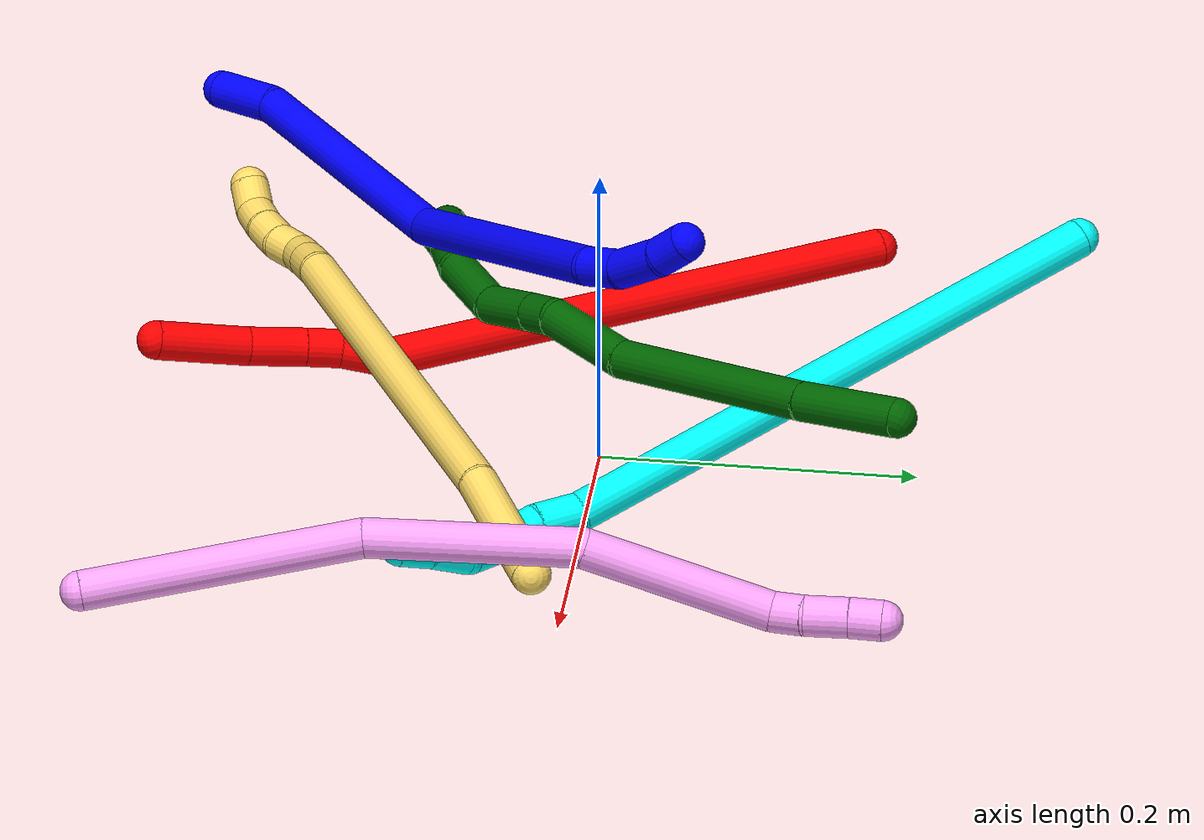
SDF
<sdf version="1.7">
 <world name="default">
  <plugin name="TubeGeneratorPlugin" filename="libtube_generator_plugin.so"/>
  <model name="photoneo_s_sensor">
   <static>1</static>
   <pose>0 0 2 1.57079 1.57079 3.14159</pose>
   <link name="link">
    <inertial><mass>0.1</mass></inertial>
    <sensor name="sensor" type="depth">
     <update_rate>30</update_rate>
     <camera>
      <horizontal_fov>1.22</horizontal_fov>
      <image><width>1920</width><height>1200</height><format>B8G8R8</format></image>
      <clip><near>0.1</near><far>4</far></clip>
      <depth_camera><output>points</output></depth_camera>
     </camera>
     <plugin name="camera_plugin" filename="libgazebo_ros_depth_camera.so">
      <baseline>0.2</baseline>
      <alwaysOn>1</alwaysOn>
      <updateRate>0.0</updateRate>
      <cameraName>camera_ir</cameraName>
      <imageTopicName>/camera/color/image_raw</imageTopicName>
      <cameraInfoTopicName>/camera/color/camera_info</cameraInfoTopicName>
      <depthImageTopicName>/camera/depth/image_raw</depthImageTopicName>
      <depthImageCameraInfoTopicName>/camera/depth/camera_info</depthImageCameraInfoTopicName>
      <pointCloudTopicName>/camera/depth/points</pointCloudTopicName>
      <frameName>fr_optical</frameName>
      <pointCloudCutoff>0.1</pointCloudCutoff>
      <pointCloudCutoffMax>2.0</pointCloudCutoffMax>
      <distortionK1>0</distortionK1>
      <distortionK2>0</distortionK2>
      <distortionK3>0</distortionK3>
      <distortionT1>0</distortionT1>
      <distortionT2>0</distortionT2>
      <CxPrime>0</CxPrime>
      <Cx>0</Cx>
      <Cy>0</Cy>
      <focalLength>0</focalLength>
      <hackBaseline>0</hackBaseline>
     </plugin>
    </sensor>
   </link>
  </model>
  <gravity>0 0 -9.8</gravity>
  <magnetic_field>6e-06 2.3e-05 -4.2e-05</magnetic_field>
  <atmosphere type="adiabatic"/>
  <physics name="default_physics" default="0" type="ode">
   <max_step_size>0.003</max_step_size>
   <real_time_factor>1</real_time_factor>
   <real_time_update_rate>1000</real_time_update_rate>
   <max_contacts>10000</max_contacts>
   <ode>
    <solver>
     <type>quick</type>
     <iters>100</iters>
     <sor>1.3</sor>
     <use_dynamic_moi_rescaling>0</use_dynamic_moi_rescaling>
    </solver>
    <constraints>
     <contact_max_correcting_vel>0</contact_max_correcting_vel>
     <contact_surface_layer>0.001</contact_surface_layer>
     <cfm>0</cfm>
     <erp>0.2</erp>
    </constraints>
   </ode>
  </physics>
  <scene><ambient>0.4 0.4 0.4 1</ambient><background>0.7 0.7 0.7 1</background><shadows>0</shadows></scene>
  <audio><device>default</device></audio>
  <spherical_coordinates>
   <surface_model>EARTH_WGS84</surface_model>
   <latitude_deg>0</latitude_deg>
   <longitude_deg>0</longitude_deg>
   <elevation>0</elevation>
   <heading_deg>0</heading_deg>
  </spherical_coordinates>
  <model name="bin">
   <static>1</static>
   <link name="bottom">
    <collision name="collision-bottom">
     <pose>0 0 -0.01 0 -0 0</pose>
     <geometry><box><size>0.8 0.6 0.02</size></box></geometry>
     <surface>
      <friction><ode><mu>100</mu><mu2>100</mu2></ode></friction>
      <contact><collide_bitmask>65535</collide_bitmask></contact>
     </surface>
    </collision>
   </link>
   <link name="west_wall">
    <collision name="collision-west_wall">
     <pose>-0.41 0 0.1 0 -0 0</pose>
     <geometry><box><size>0.02 0.6 0.2</size></box></geometry>
     <surface>
      <friction><ode><mu>100</mu><mu2>100</mu2></ode></friction>
      <contact><collide_bitmask>65535</collide_bitmask></contact>
     </surface>
    </collision>
   </link>
   <link name="east_wall">
    <collision name="collision-east_wall">
     <pose>0.41 0 0.1 0 -0 0</pose>
     <geometry><box><size>0.02 0.6 0.2</size></box></geometry>
     <surface>
      <friction><ode><mu>100</mu><mu2>100</mu2></ode></friction>
      <contact><collide_bitmask>65535</collide_bitmask></contact>
     </surface>
    </collision>
   </link>
   <link name="south_wall">
    <collision name="collision-south_wall">
     <pose>0 -0.31 0.1 0 -0 0</pose>
     <geometry><box><size>0.8 0.02 0.2</size></box></geometry>
     <surface>
      <friction><ode><mu>100</mu><mu2>100</mu2></ode></friction>
      <contact><collide_bitmask>65535</collide_bitmask></contact>
     </surface>
    </collision>
   </link>
   <link name="north_wall">
    <collision name="collision-north_wall">
     <pose>0 0.31 0.1 0 -0 0</pose>
     <geometry><box><size>0.8 0.02 0.2</size></box></geometry>
     <surface>
      <friction><ode><mu>100</mu><mu2>100</mu2></ode></friction>
      <contact><collide_bitmask>65535</collide_bitmask></contact>
     </surface>
    </collision>
   </link>
  </model>
  <model name="1">
   <static>0</static>
   <link name="1">
    <collision name="collision-cylinder-e_1_1_4">
     <pose>2e-05 0.000368 0.022012 -0.016731 0.000888 -7e-06</pose>
     <geometry><cylinder><radius>0.0125</radius><length>0.04403</length></cylinder></geometry>
     <surface>
      <friction><ode><mu>1.16</mu><mu2>1.16</mu2><slip1>0</slip1><slip2>0</slip2></ode></friction>
      <contact><ode><kp>1e+06</kp><kd>1</kd><max_vel>0</max_vel><min_depth>0.001</min_depth></ode></contact>
     </surface>
    </collision>
    <visual name="visual-cylinder-e_1_1_4">
     <pose>2e-05 0.000368 0.022012 -0.016731 0.000888 -7e-06</pose>
     <geometry><cylinder><radius>0.0125</radius><length>0.04403</length></cylinder></geometry>
     <material><ambient>0 0 1 1</ambient></material>
    </visual>
    <collision name="collision-cylinder-e_2_4_5">
     <pose>-0.023304 -0.002079 0.120374 0.036866 -0.296524 -0.005507</pose>
     <geometry><cylinder><radius>0.0125</radius><length>0.159778</length></cylinder></geometry>
     <surface>
      <friction><ode><mu>1.16</mu><mu2>1.16</mu2><slip1>0</slip1><slip2>0</slip2></ode></friction>
      <contact><ode><kp>1e+06</kp><kd>1</kd><max_vel>0</max_vel><min_depth>0.001</min_depth></ode></contact>
     </surface>
    </collision>
    <visual name="visual-cylinder-e_2_4_5">
     <pose>-0.023304 -0.002079 0.120374 0.036866 -0.296524 -0.005507</pose>
     <geometry><cylinder><radius>0.0125</radius><length>0.159778</length></cylinder></geometry>
     <material><ambient>0 0 1 1</ambient></material>
    </visual>
    <collision name="collision-cylinder-e_3_5_6">
     <pose>-0.054449 0.040064 0.293041 -0.43673 -0.07326 0.016264</pose>
     <geometry><cylinder><radius>0.0125</radius><length>0.213158</length></cylinder></geometry>
     <surface>
      <friction><ode><mu>1.16</mu><mu2>1.16</mu2><slip1>0</slip1><slip2>0</slip2></ode></friction>
      <contact><ode><kp>1e+06</kp><kd>1</kd><max_vel>0</max_vel><min_depth>0.001</min_depth></ode></contact>
     </surface>
    </collision>
    <visual name="visual-cylinder-e_3_5_6">
     <pose>-0.054449 0.040064 0.293041 -0.43673 -0.07326 0.016264</pose>
     <geometry><cylinder><radius>0.0125</radius><length>0.213158</length></cylinder></geometry>
     <material><ambient>0 0 1 1</ambient></material>
    </visual>
    <collision name="collision-cylinder-e_4_6_7">
     <pose>-0.060797 0.087384 0.402421 -0.178726 0.108998 -0.009776</pose>
     <geometry><cylinder><radius>0.0125</radius><length>0.02671</length></cylinder></geometry>
     <surface>
      <friction><ode><mu>1.16</mu><mu2>1.16</mu2><slip1>0</slip1><slip2>0</slip2></ode></friction>
      <contact><ode><kp>1e+06</kp><kd>1</kd><max_vel>0</max_vel><min_depth>0.001</min_depth></ode></contact>
     </surface>
    </collision>
    <visual name="visual-cylinder-e_4_6_7">
     <pose>-0.060797 0.087384 0.402421 -0.178726 0.108998 -0.009776</pose>
     <geometry><cylinder><radius>0.0125</radius><length>0.02671</length></cylinder></geometry>
     <material><ambient>0 0 1 1</ambient></material>
    </visual>
    <collision name="collision-cylinder-e_5_7_8">
     <pose>-0.053374 0.095472 0.430909 -0.355575 0.348083 -0.063163</pose>
     <geometry><cylinder><radius>0.0125</radius><length>0.035004</length></cylinder></geometry>
     <surface>
      <friction><ode><mu>1.16</mu><mu2>1.16</mu2><slip1>0</slip1><slip2>0</slip2></ode></friction>
      <contact><ode><kp>1e+06</kp><kd>1</kd><max_vel>0</max_vel><min_depth>0.001</min_depth></ode></contact>
     </surface>
    </collision>
    <visual name="visual-cylinder-e_5_7_8">
     <pose>-0.053374 0.095472 0.430909 -0.355575 0.348083 -0.063163</pose>
     <geometry><cylinder><radius>0.0125</radius><length>0.035004</length></cylinder></geometry>
     <material><ambient>0 0 1 1</ambient></material>
    </visual>
    <collision name="collision-cylinder-e_6_8_2">
     <pose>-0.041522 0.10431 0.454661 -0.357487 0.584504 -0.10861</pose>
     <geometry><cylinder><radius>0.0125</radius><length>0.021321</length></cylinder></geometry>
     <surface>
      <friction><ode><mu>1.16</mu><mu2>1.16</mu2><slip1>0</slip1><slip2>0</slip2></ode></friction>
      <contact><ode><kp>1e+06</kp><kd>1</kd><max_vel>0</max_vel><min_depth>0.001</min_depth></ode></contact>
     </surface>
    </collision>
    <visual name="visual-cylinder-e_6_8_2">
     <pose>-0.041522 0.10431 0.454661 -0.357487 0.584504 -0.10861</pose>
     <geometry><cylinder><radius>0.0125</radius><length>0.021321</length></cylinder></geometry>
     <material><ambient>0 0 1 1</ambient></material>
    </visual>
    <collision name="collision-sphere-2">
     <pose>-0.03564 0.107421 0.462989 0 -0 0</pose>
     <geometry><sphere><radius>0.0125</radius></sphere></geometry>
     <surface>
      <friction><ode><mu>1.16</mu><mu2>1.16</mu2><slip1>0</slip1><slip2>0</slip2></ode></friction>
      <contact><ode><kp>1e+06</kp><kd>1</kd><max_vel>0</max_vel><min_depth>0.001</min_depth></ode></contact>
     </surface>
    </collision>
    <visual name="visual-sphere-2">
     <pose>-0.03564 0.107421 0.462989 0 -0 0</pose>
     <geometry><sphere><radius>0.0125</radius></sphere></geometry>
     <material><ambient>0 0 1 1</ambient></material>
    </visual>
    <collision name="collision-sphere-4">
     <pose>3.9e-05 0.000737 0.044023 0 -0 0</pose>
     <geometry><sphere><radius>0.0125</radius></sphere></geometry>
     <surface>
      <friction><ode><mu>1.16</mu><mu2>1.16</mu2><slip1>0</slip1><slip2>0</slip2></ode></friction>
      <contact><ode><kp>1e+06</kp><kd>1</kd><max_vel>0</max_vel><min_depth>0.001</min_depth></ode></contact>
     </surface>
    </collision>
    <visual name="visual-sphere-4">
     <pose>3.9e-05 0.000737 0.044023 0 -0 0</pose>
     <geometry><sphere><radius>0.0125</radius></sphere></geometry>
     <material><ambient>0 0 1 1</ambient></material>
    </visual>
    <collision name="collision-sphere-1">
     <geometry><sphere><radius>0.0125</radius></sphere></geometry>
     <surface>
      <friction><ode><mu>1.16</mu><mu2>1.16</mu2><slip1>0</slip1><slip2>0</slip2></ode></friction>
      <contact><ode><kp>1e+06</kp><kd>1</kd><max_vel>0</max_vel><min_depth>0.001</min_depth></ode></contact>
     </surface>
    </collision>
    <visual name="visual-sphere-1">
     <geometry><sphere><radius>0.0125</radius></sphere></geometry>
     <material><ambient>0 0 1 1</ambient></material>
    </visual>
    <collision name="collision-sphere-8">
     <pose>-0.047404 0.101199 0.446332 0 -0 0</pose>
     <geometry><sphere><radius>0.0125</radius></sphere></geometry>
     <surface>
      <friction><ode><mu>1.16</mu><mu2>1.16</mu2><slip1>0</slip1><slip2>0</slip2></ode></friction>
      <contact><ode><kp>1e+06</kp><kd>1</kd><max_vel>0</max_vel><min_depth>0.001</min_depth></ode></contact>
     </surface>
    </collision>
    <visual name="visual-sphere-8">
     <pose>-0.047404 0.101199 0.446332 0 -0 0</pose>
     <geometry><sphere><radius>0.0125</radius></sphere></geometry>
     <material><ambient>0 0 1 1</ambient></material>
    </visual>
    <collision name="collision-sphere-5">
     <pose>-0.046648 -0.004895 0.196724 0 -0 0</pose>
     <geometry><sphere><radius>0.0125</radius></sphere></geometry>
     <surface>
      <friction><ode><mu>1.16</mu><mu2>1.16</mu2><slip1>0</slip1><slip2>0</slip2></ode></friction>
      <contact><ode><kp>1e+06</kp><kd>1</kd><max_vel>0</max_vel><min_depth>0.001</min_depth></ode></contact>
     </surface>
    </collision>
    <visual name="visual-sphere-5">
     <pose>-0.046648 -0.004895 0.196724 0 -0 0</pose>
     <geometry><sphere><radius>0.0125</radius></sphere></geometry>
     <material><ambient>0 0 1 1</ambient></material>
    </visual>
    <collision name="collision-sphere-6">
     <pose>-0.06225 0.085024 0.389357 0 -0 0</pose>
     <geometry><sphere><radius>0.0125</radius></sphere></geometry>
     <surface>
      <friction><ode><mu>1.16</mu><mu2>1.16</mu2><slip1>0</slip1><slip2>0</slip2></ode></friction>
      <contact><ode><kp>1e+06</kp><kd>1</kd><max_vel>0</max_vel><min_depth>0.001</min_depth></ode></contact>
     </surface>
    </collision>
    <visual name="visual-sphere-6">
     <pose>-0.06225 0.085024 0.389357 0 -0 0</pose>
     <geometry><sphere><radius>0.0125</radius></sphere></geometry>
     <material><ambient>0 0 1 1</ambient></material>
    </visual>
    <collision name="collision-sphere-7">
     <pose>-0.059344 0.089744 0.415486 0 -0 0</pose>
     <geometry><sphere><radius>0.0125</radius></sphere></geometry>
     <surface>
      <friction><ode><mu>1.16</mu><mu2>1.16</mu2><slip1>0</slip1><slip2>0</slip2></ode></friction>
      <contact><ode><kp>1e+06</kp><kd>1</kd><max_vel>0</max_vel><min_depth>0.001</min_depth></ode></contact>
     </surface>
    </collision>
    <visual name="visual-sphere-7">
     <pose>-0.059344 0.089744 0.415486 0 -0 0</pose>
     <geometry><sphere><radius>0.0125</radius></sphere></geometry>
     <material><ambient>0 0 1 1</ambient></material>
    </visual>
    <inertial>
     <pose>-0.039412 0.032248 0.236384 0 -0 0</pose>
     <mass>0.5</mass>
     <inertia>
      <ixx>0.00117</ixx>
      <ixy>0</ixy>
      <ixz>0</ixz>
      <iyy>0.001122</iyy>
      <iyz>0</iyz>
      <izz>-0.00014</izz>
     </inertia>
    </inertial>
   </link>
   <pose>-0.291661 -0.288515 0.08476 1.47413 -0.736259 2.67395</pose>
  </model>
  <model name="2">
   <static>0</static>
   <link name="2">
    <collision name="collision-cylinder-e_1_1_4">
     <pose>0.079349 -0.143141 -0.059236 1.96317 0.473373 0.692643</pose>
     <geometry><cylinder><radius>0.0125</radius><length>0.348106</length></cylinder></geometry>
     <surface>
      <friction><ode><mu>1.16</mu><mu2>1.16</mu2><slip1>0</slip1><slip2>0</slip2></ode></friction>
      <contact><ode><kp>1e+06</kp><kd>1</kd><max_vel>0</max_vel><min_depth>0.001</min_depth></ode></contact>
     </surface>
    </collision>
    <visual name="visual-cylinder-e_1_1_4">
     <pose>0.079349 -0.143141 -0.059236 1.96317 0.473373 0.692643</pose>
     <geometry><cylinder><radius>0.0125</radius><length>0.348106</length></cylinder></geometry>
     <material><ambient>1 0 0 1</ambient></material>
    </visual>
    <collision name="collision-cylinder-e_2_4_5">
     <pose>0.169554 -0.293169 -0.126534 2.43457 0.797166 1.7025</pose>
     <geometry><cylinder><radius>0.0125</radius><length>0.03035</length></cylinder></geometry>
     <surface>
      <friction><ode><mu>1.16</mu><mu2>1.16</mu2><slip1>0</slip1><slip2>0</slip2></ode></friction>
      <contact><ode><kp>1e+06</kp><kd>1</kd><max_vel>0</max_vel><min_depth>0.001</min_depth></ode></contact>
     </surface>
    </collision>
    <visual name="visual-cylinder-e_2_4_5">
     <pose>0.169554 -0.293169 -0.126534 2.43457 0.797166 1.7025</pose>
     <geometry><cylinder><radius>0.0125</radius><length>0.03035</length></cylinder></geometry>
     <material><ambient>1 0 0 1</ambient></material>
    </visual>
    <collision name="collision-cylinder-e_3_5_6">
     <pose>0.187676 -0.307168 -0.140119 2.2312 0.678892 1.2499</pose>
     <geometry><cylinder><radius>0.0125</radius><length>0.023142</length></cylinder></geometry>
     <surface>
      <friction><ode><mu>1.16</mu><mu2>1.16</mu2><slip1>0</slip1><slip2>0</slip2></ode></friction>
      <contact><ode><kp>1e+06</kp><kd>1</kd><max_vel>0</max_vel><min_depth>0.001</min_depth></ode></contact>
     </surface>
    </collision>
    <visual name="visual-cylinder-e_3_5_6">
     <pose>0.187676 -0.307168 -0.140119 2.2312 0.678892 1.2499</pose>
     <geometry><cylinder><radius>0.0125</radius><length>0.023142</length></cylinder></geometry>
     <material><ambient>1 0 0 1</ambient></material>
    </visual>
    <collision name="collision-cylinder-e_4_6_7">
     <pose>0.206418 -0.32613 -0.154321 2.20284 0.663281 1.19293</pose>
     <geometry><cylinder><radius>0.0125</radius><length>0.037278</length></cylinder></geometry>
     <surface>
      <friction><ode><mu>1.16</mu><mu2>1.16</mu2><slip1>0</slip1><slip2>0</slip2></ode></friction>
      <contact><ode><kp>1e+06</kp><kd>1</kd><max_vel>0</max_vel><min_depth>0.001</min_depth></ode></contact>
     </surface>
    </collision>
    <visual name="visual-cylinder-e_4_6_7">
     <pose>0.206418 -0.32613 -0.154321 2.20284 0.663281 1.19293</pose>
     <geometry><cylinder><radius>0.0125</radius><length>0.037278</length></cylinder></geometry>
     <material><ambient>1 0 0 1</ambient></material>
    </visual>
    <collision name="collision-cylinder-e_5_7_2">
     <pose>0.232594 -0.358515 -0.180211 2.26843 0.50179 1.00456</pose>
     <geometry><cylinder><radius>0.0125</radius><length>0.061124</length></cylinder></geometry>
     <surface>
      <friction><ode><mu>1.16</mu><mu2>1.16</mu2><slip1>0</slip1><slip2>0</slip2></ode></friction>
      <contact><ode><kp>1e+06</kp><kd>1</kd><max_vel>0</max_vel><min_depth>0.001</min_depth></ode></contact>
     </surface>
    </collision>
    <visual name="visual-cylinder-e_5_7_2">
     <pose>0.232594 -0.358515 -0.180211 2.26843 0.50179 1.00456</pose>
     <geometry><cylinder><radius>0.0125</radius><length>0.061124</length></cylinder></geometry>
     <material><ambient>1 0 0 1</ambient></material>
    </visual>
    <collision name="collision-sphere-2">
     <pose>0.247294 -0.379049 -0.197423 0 -0 0</pose>
     <geometry><sphere><radius>0.0125</radius></sphere></geometry>
     <surface>
      <friction><ode><mu>1.16</mu><mu2>1.16</mu2><slip1>0</slip1><slip2>0</slip2></ode></friction>
      <contact><ode><kp>1e+06</kp><kd>1</kd><max_vel>0</max_vel><min_depth>0.001</min_depth></ode></contact>
     </surface>
    </collision>
    <visual name="visual-sphere-2">
     <pose>0.247294 -0.379049 -0.197423 0 -0 0</pose>
     <geometry><sphere><radius>0.0125</radius></sphere></geometry>
     <material><ambient>1 0 0 1</ambient></material>
    </visual>
    <collision name="collision-sphere-7">
     <pose>0.217894 -0.33798 -0.162998 0 -0 0</pose>
     <geometry><sphere><radius>0.0125</radius></sphere></geometry>
     <surface>
      <friction><ode><mu>1.16</mu><mu2>1.16</mu2><slip1>0</slip1><slip2>0</slip2></ode></friction>
      <contact><ode><kp>1e+06</kp><kd>1</kd><max_vel>0</max_vel><min_depth>0.001</min_depth></ode></contact>
     </surface>
    </collision>
    <visual name="visual-sphere-7">
     <pose>0.217894 -0.33798 -0.162998 0 -0 0</pose>
     <geometry><sphere><radius>0.0125</radius></sphere></geometry>
     <material><ambient>1 0 0 1</ambient></material>
    </visual>
    <collision name="collision-sphere-6">
     <pose>0.194942 -0.31428 -0.145644 0 -0 0</pose>
     <geometry><sphere><radius>0.0125</radius></sphere></geometry>
     <surface>
      <friction><ode><mu>1.16</mu><mu2>1.16</mu2><slip1>0</slip1><slip2>0</slip2></ode></friction>
      <contact><ode><kp>1e+06</kp><kd>1</kd><max_vel>0</max_vel><min_depth>0.001</min_depth></ode></contact>
     </surface>
    </collision>
    <visual name="visual-sphere-6">
     <pose>0.194942 -0.31428 -0.145644 0 -0 0</pose>
     <geometry><sphere><radius>0.0125</radius></sphere></geometry>
     <material><ambient>1 0 0 1</ambient></material>
    </visual>
    <collision name="collision-sphere-5">
     <pose>0.18041 -0.300057 -0.134595 0 -0 0</pose>
     <geometry><sphere><radius>0.0125</radius></sphere></geometry>
     <surface>
      <friction><ode><mu>1.16</mu><mu2>1.16</mu2><slip1>0</slip1><slip2>0</slip2></ode></friction>
      <contact><ode><kp>1e+06</kp><kd>1</kd><max_vel>0</max_vel><min_depth>0.001</min_depth></ode></contact>
     </surface>
    </collision>
    <visual name="visual-sphere-5">
     <pose>0.18041 -0.300057 -0.134595 0 -0 0</pose>
     <geometry><sphere><radius>0.0125</radius></sphere></geometry>
     <material><ambient>1 0 0 1</ambient></material>
    </visual>
    <collision name="collision-sphere-1">
     <geometry><sphere><radius>0.0125</radius></sphere></geometry>
     <surface>
      <friction><ode><mu>1.16</mu><mu2>1.16</mu2><slip1>0</slip1><slip2>0</slip2></ode></friction>
      <contact><ode><kp>1e+06</kp><kd>1</kd><max_vel>0</max_vel><min_depth>0.001</min_depth></ode></contact>
     </surface>
    </collision>
    <visual name="visual-sphere-1">
     <geometry><sphere><radius>0.0125</radius></sphere></geometry>
     <material><ambient>1 0 0 1</ambient></material>
    </visual>
    <collision name="collision-sphere-4">
     <pose>0.158699 -0.286281 -0.118472 0 -0 0</pose>
     <geometry><sphere><radius>0.0125</radius></sphere></geometry>
     <surface>
      <friction><ode><mu>1.16</mu><mu2>1.16</mu2><slip1>0</slip1><slip2>0</slip2></ode></friction>
      <contact><ode><kp>1e+06</kp><kd>1</kd><max_vel>0</max_vel><min_depth>0.001</min_depth></ode></contact>
     </surface>
    </collision>
    <visual name="visual-sphere-4">
     <pose>0.158699 -0.286281 -0.118472 0 -0 0</pose>
     <geometry><sphere><radius>0.0125</radius></sphere></geometry>
     <material><ambient>1 0 0 1</ambient></material>
    </visual>
    <inertial>
     <pose>0.118046 -0.199811 -0.088943 0 -0 0</pose>
     <mass>0.5</mass>
     <inertia>
      <ixx>0.004478</ixx>
      <ixy>0</ixy>
      <ixz>0</ixz>
      <iyy>0.001914</iyy>
      <iyz>0</iyz>
      <izz>0.001281</izz>
     </inertia>
    </inertial>
   </link>
   <pose>-0.264957 0.150574 0.011499 2.89554 0.277325 -2.10203</pose>
  </model>
  <model name="3">
   <static>0</static>
   <link name="3">
    <collision name="collision-cylinder-e_1_1_4">
     <pose>0.086215 -0.115543 -0.120668 2.37789 0.47641 1.0877</pose>
     <geometry><cylinder><radius>0.0125</radius><length>0.375999</length></cylinder></geometry>
     <surface>
      <friction><ode><mu>1.16</mu><mu2>1.16</mu2><slip1>0</slip1><slip2>0</slip2></ode></friction>
      <contact><ode><kp>1e+06</kp><kd>1</kd><max_vel>0</max_vel><min_depth>0.001</min_depth></ode></contact>
     </surface>
    </collision>
    <visual name="visual-cylinder-e_1_1_4">
     <pose>0.086215 -0.115543 -0.120668 2.37789 0.47641 1.0877</pose>
     <geometry><cylinder><radius>0.0125</radius><length>0.375999</length></cylinder></geometry>
     <material><ambient>0.003922 1 0.996078 1</ambient></material>
    </visual>
    <collision name="collision-cylinder-e_2_4_5">
     <pose>0.176208 -0.241464 -0.24983 2.25671 0.274583 0.567503</pose>
     <geometry><cylinder><radius>0.0125</radius><length>0.027868</length></cylinder></geometry>
     <surface>
      <friction><ode><mu>1.16</mu><mu2>1.16</mu2><slip1>0</slip1><slip2>0</slip2></ode></friction>
      <contact><ode><kp>1e+06</kp><kd>1</kd><max_vel>0</max_vel><min_depth>0.001</min_depth></ode></contact>
     </surface>
    </collision>
    <visual name="visual-cylinder-e_2_4_5">
     <pose>0.176208 -0.241464 -0.24983 2.25671 0.274583 0.567503</pose>
     <geometry><cylinder><radius>0.0125</radius><length>0.027868</length></cylinder></geometry>
     <material><ambient>0.003922 1 0.996078 1</ambient></material>
    </visual>
    <collision name="collision-cylinder-e_3_5_6">
     <pose>0.185914 -0.260113 -0.266241 2.33431 0.477775 1.03647</pose>
     <geometry><cylinder><radius>0.0125</radius><length>0.025785</length></cylinder></geometry>
     <surface>
      <friction><ode><mu>1.16</mu><mu2>1.16</mu2><slip1>0</slip1><slip2>0</slip2></ode></friction>
      <contact><ode><kp>1e+06</kp><kd>1</kd><max_vel>0</max_vel><min_depth>0.001</min_depth></ode></contact>
     </surface>
    </collision>
    <visual name="visual-cylinder-e_3_5_6">
     <pose>0.185914 -0.260113 -0.266241 2.33431 0.477775 1.03647</pose>
     <geometry><cylinder><radius>0.0125</radius><length>0.025785</length></cylinder></geometry>
     <material><ambient>0.003922 1 0.996078 1</ambient></material>
    </visual>
    <collision name="collision-cylinder-e_4_6_7">
     <pose>0.198004 -0.278644 -0.278945 2.0074 0.498406 0.760313</pose>
     <geometry><cylinder><radius>0.0125</radius><length>0.02578</length></cylinder></geometry>
     <surface>
      <friction><ode><mu>1.16</mu><mu2>1.16</mu2><slip1>0</slip1><slip2>0</slip2></ode></friction>
      <contact><ode><kp>1e+06</kp><kd>1</kd><max_vel>0</max_vel><min_depth>0.001</min_depth></ode></contact>
     </surface>
    </collision>
    <visual name="visual-cylinder-e_4_6_7">
     <pose>0.198004 -0.278644 -0.278945 2.0074 0.498406 0.760313</pose>
     <geometry><cylinder><radius>0.0125</radius><length>0.02578</length></cylinder></geometry>
     <material><ambient>0.003922 1 0.996078 1</ambient></material>
    </visual>
    <collision name="collision-cylinder-e_5_7_8">
     <pose>0.204475 -0.300374 -0.287803 1.91178 0.025393 0.035952</pose>
     <geometry><cylinder><radius>0.0125</radius><length>0.02435</length></cylinder></geometry>
     <surface>
      <friction><ode><mu>1.16</mu><mu2>1.16</mu2><slip1>0</slip1><slip2>0</slip2></ode></friction>
      <contact><ode><kp>1e+06</kp><kd>1</kd><max_vel>0</max_vel><min_depth>0.001</min_depth></ode></contact>
     </surface>
    </collision>
    <visual name="visual-cylinder-e_5_7_8">
     <pose>0.204475 -0.300374 -0.287803 1.91178 0.025393 0.035952</pose>
     <geometry><cylinder><radius>0.0125</radius><length>0.02435</length></cylinder></geometry>
     <material><ambient>0.003922 1 0.996078 1</ambient></material>
    </visual>
    <collision name="collision-cylinder-e_6_8_2">
     <pose>0.204391 -0.320359 -0.297309 2.13901 -0.038834 -0.070847</pose>
     <geometry><cylinder><radius>0.0125</radius><length>0.020218</length></cylinder></geometry>
     <surface>
      <friction><ode><mu>1.16</mu><mu2>1.16</mu2><slip1>0</slip1><slip2>0</slip2></ode></friction>
      <contact><ode><kp>1e+06</kp><kd>1</kd><max_vel>0</max_vel><min_depth>0.001</min_depth></ode></contact>
     </surface>
    </collision>
    <visual name="visual-cylinder-e_6_8_2">
     <pose>0.204391 -0.320359 -0.297309 2.13901 -0.038834 -0.070847</pose>
     <geometry><cylinder><radius>0.0125</radius><length>0.020218</length></cylinder></geometry>
     <material><ambient>0.003922 1 0.996078 1</ambient></material>
    </visual>
    <collision name="collision-sphere-2">
     <pose>0.203999 -0.328873 -0.302745 0 -0 0</pose>
     <geometry><sphere><radius>0.0125</radius></sphere></geometry>
     <surface>
      <friction><ode><mu>1.16</mu><mu2>1.16</mu2><slip1>0</slip1><slip2>0</slip2></ode></friction>
      <contact><ode><kp>1e+06</kp><kd>1</kd><max_vel>0</max_vel><min_depth>0.001</min_depth></ode></contact>
     </surface>
    </collision>
    <visual name="visual-sphere-2">
     <pose>0.203999 -0.328873 -0.302745 0 -0 0</pose>
     <geometry><sphere><radius>0.0125</radius></sphere></geometry>
     <material><ambient>0.003922 1 0.996078 1</ambient></material>
    </visual>
    <collision name="collision-sphere-4">
     <pose>0.17243 -0.231085 -0.241335 0 -0 0</pose>
     <geometry><sphere><radius>0.0125</radius></sphere></geometry>
     <surface>
      <friction><ode><mu>1.16</mu><mu2>1.16</mu2><slip1>0</slip1><slip2>0</slip2></ode></friction>
      <contact><ode><kp>1e+06</kp><kd>1</kd><max_vel>0</max_vel><min_depth>0.001</min_depth></ode></contact>
     </surface>
    </collision>
    <visual name="visual-sphere-4">
     <pose>0.17243 -0.231085 -0.241335 0 -0 0</pose>
     <geometry><sphere><radius>0.0125</radius></sphere></geometry>
     <material><ambient>0.003922 1 0.996078 1</ambient></material>
    </visual>
    <collision name="collision-sphere-1">
     <geometry><sphere><radius>0.0125</radius></sphere></geometry>
     <surface>
      <friction><ode><mu>1.16</mu><mu2>1.16</mu2><slip1>0</slip1><slip2>0</slip2></ode></friction>
      <contact><ode><kp>1e+06</kp><kd>1</kd><max_vel>0</max_vel><min_depth>0.001</min_depth></ode></contact>
     </surface>
    </collision>
    <visual name="visual-sphere-1">
     <geometry><sphere><radius>0.0125</radius></sphere></geometry>
     <material><ambient>0.003922 1 0.996078 1</ambient></material>
    </visual>
    <collision name="collision-sphere-8">
     <pose>0.204784 -0.311844 -0.291873 0 -0 0</pose>
     <geometry><sphere><radius>0.0125</radius></sphere></geometry>
     <surface>
      <friction><ode><mu>1.16</mu><mu2>1.16</mu2><slip1>0</slip1><slip2>0</slip2></ode></friction>
      <contact><ode><kp>1e+06</kp><kd>1</kd><max_vel>0</max_vel><min_depth>0.001</min_depth></ode></contact>
     </surface>
    </collision>
    <visual name="visual-sphere-8">
     <pose>0.204784 -0.311844 -0.291873 0 -0 0</pose>
     <geometry><sphere><radius>0.0125</radius></sphere></geometry>
     <material><ambient>0.003922 1 0.996078 1</ambient></material>
    </visual>
    <collision name="collision-sphere-5">
     <pose>0.179986 -0.251842 -0.258325 0 -0 0</pose>
     <geometry><sphere><radius>0.0125</radius></sphere></geometry>
     <surface>
      <friction><ode><mu>1.16</mu><mu2>1.16</mu2><slip1>0</slip1><slip2>0</slip2></ode></friction>
      <contact><ode><kp>1e+06</kp><kd>1</kd><max_vel>0</max_vel><min_depth>0.001</min_depth></ode></contact>
     </surface>
    </collision>
    <visual name="visual-sphere-5">
     <pose>0.179986 -0.251842 -0.258325 0 -0 0</pose>
     <geometry><sphere><radius>0.0125</radius></sphere></geometry>
     <material><ambient>0.003922 1 0.996078 1</ambient></material>
    </visual>
    <collision name="collision-sphere-6">
     <pose>0.191842 -0.268384 -0.274158 0 -0 0</pose>
     <geometry><sphere><radius>0.0125</radius></sphere></geometry>
     <surface>
      <friction><ode><mu>1.16</mu><mu2>1.16</mu2><slip1>0</slip1><slip2>0</slip2></ode></friction>
      <contact><ode><kp>1e+06</kp><kd>1</kd><max_vel>0</max_vel><min_depth>0.001</min_depth></ode></contact>
     </surface>
    </collision>
    <visual name="visual-sphere-6">
     <pose>0.191842 -0.268384 -0.274158 0 -0 0</pose>
     <geometry><sphere><radius>0.0125</radius></sphere></geometry>
     <material><ambient>0.003922 1 0.996078 1</ambient></material>
    </visual>
    <collision name="collision-sphere-7">
     <pose>0.204166 -0.288903 -0.283733 0 -0 0</pose>
     <geometry><sphere><radius>0.0125</radius></sphere></geometry>
     <surface>
      <friction><ode><mu>1.16</mu><mu2>1.16</mu2><slip1>0</slip1><slip2>0</slip2></ode></friction>
      <contact><ode><kp>1e+06</kp><kd>1</kd><max_vel>0</max_vel><min_depth>0.001</min_depth></ode></contact>
     </surface>
    </collision>
    <visual name="visual-sphere-7">
     <pose>0.204166 -0.288903 -0.283733 0 -0 0</pose>
     <geometry><sphere><radius>0.0125</radius></sphere></geometry>
     <material><ambient>0.003922 1 0.996078 1</ambient></material>
    </visual>
    <inertial>
     <pose>0.112674 -0.155709 -0.158817 0 -0 0</pose>
     <mass>0.5</mass>
     <inertia>
      <ixx>0.005362</ixx>
      <ixy>0</ixy>
      <ixz>0</ixz>
      <iyy>0.003231</iyy>
      <iyz>0</iyz>
      <izz>0.000676</izz>
     </inertia>
    </inertial>
   </link>
   <pose>-0.127506 0.288526 0.106566 -0.752129 0.428802 0.238872</pose>
  </model>
  <model name="4">
   <static>0</static>
   <link name="4">
    <collision name="collision-cylinder-e_1_1_4">
     <pose>0.028218 -0.018775 -0.080373 2.91211 0.329421 1.92909</pose>
     <geometry><cylinder><radius>0.0125</radius><length>0.174455</length></cylinder></geometry>
     <surface>
      <friction><ode><mu>1.16</mu><mu2>1.16</mu2><slip1>0</slip1><slip2>0</slip2></ode></friction>
      <contact><ode><kp>1e+06</kp><kd>1</kd><max_vel>0</max_vel><min_depth>0.001</min_depth></ode></contact>
     </surface>
    </collision>
    <visual name="visual-cylinder-e_1_1_4">
     <pose>0.028218 -0.018775 -0.080373 2.91211 0.329421 1.92909</pose>
     <geometry><cylinder><radius>0.0125</radius><length>0.174455</length></cylinder></geometry>
     <material><ambient>1 0.65098 0.996078 1</ambient></material>
    </visual>
    <collision name="collision-cylinder-e_2_4_5">
     <pose>0.061019 -0.031966 -0.228855 -3.05979 0.066978 -1.37198</pose>
     <geometry><cylinder><radius>0.0125</radius><length>0.13698</length></cylinder></geometry>
     <surface>
      <friction><ode><mu>1.16</mu><mu2>1.16</mu2><slip1>0</slip1><slip2>0</slip2></ode></friction>
      <contact><ode><kp>1e+06</kp><kd>1</kd><max_vel>0</max_vel><min_depth>0.001</min_depth></ode></contact>
     </surface>
    </collision>
    <visual name="visual-cylinder-e_2_4_5">
     <pose>0.061019 -0.031966 -0.228855 -3.05979 0.066978 -1.37198</pose>
     <geometry><cylinder><radius>0.0125</radius><length>0.13698</length></cylinder></geometry>
     <material><ambient>1 0.65098 0.996078 1</ambient></material>
    </visual>
    <collision name="collision-cylinder-e_3_5_6">
     <pose>0.092492 -0.010187 -0.348415 -2.83666 0.462439 -1.98508</pose>
     <geometry><cylinder><radius>0.0125</radius><length>0.120542</length></cylinder></geometry>
     <surface>
      <friction><ode><mu>1.16</mu><mu2>1.16</mu2><slip1>0</slip1><slip2>0</slip2></ode></friction>
      <contact><ode><kp>1e+06</kp><kd>1</kd><max_vel>0</max_vel><min_depth>0.001</min_depth></ode></contact>
     </surface>
    </collision>
    <visual name="visual-cylinder-e_3_5_6">
     <pose>0.092492 -0.010187 -0.348415 -2.83666 0.462439 -1.98508</pose>
     <geometry><cylinder><radius>0.0125</radius><length>0.120542</length></cylinder></geometry>
     <material><ambient>1 0.65098 0.996078 1</ambient></material>
    </visual>
    <collision name="collision-cylinder-e_4_6_7">
     <pose>0.119486 0.007722 -0.410047 -2.97477 0.01013 -0.121021</pose>
     <geometry><cylinder><radius>0.0125</radius><length>0.020646</length></cylinder></geometry>
     <surface>
      <friction><ode><mu>1.16</mu><mu2>1.16</mu2><slip1>0</slip1><slip2>0</slip2></ode></friction>
      <contact><ode><kp>1e+06</kp><kd>1</kd><max_vel>0</max_vel><min_depth>0.001</min_depth></ode></contact>
     </surface>
    </collision>
    <visual name="visual-cylinder-e_4_6_7">
     <pose>0.119486 0.007722 -0.410047 -2.97477 0.01013 -0.121021</pose>
     <geometry><cylinder><radius>0.0125</radius><length>0.020646</length></cylinder></geometry>
     <material><ambient>1 0.65098 0.996078 1</ambient></material>
    </visual>
    <collision name="collision-cylinder-e_5_7_8">
     <pose>0.121999 0.010199 -0.433521 -3.08424 0.178971 -2.5227</pose>
     <geometry><cylinder><radius>0.0125</radius><length>0.027066</length></cylinder></geometry>
     <surface>
      <friction><ode><mu>1.16</mu><mu2>1.16</mu2><slip1>0</slip1><slip2>0</slip2></ode></friction>
      <contact><ode><kp>1e+06</kp><kd>1</kd><max_vel>0</max_vel><min_depth>0.001</min_depth></ode></contact>
     </surface>
    </collision>
    <visual name="visual-cylinder-e_5_7_8">
     <pose>0.121999 0.010199 -0.433521 -3.08424 0.178971 -2.5227</pose>
     <geometry><cylinder><radius>0.0125</radius><length>0.027066</length></cylinder></geometry>
     <material><ambient>1 0.65098 0.996078 1</ambient></material>
    </visual>
    <collision name="collision-cylinder-e_6_8_2">
     <pose>0.126473 0.011909 -0.456714 -3.04628 0.204728 -2.27226</pose>
     <geometry><cylinder><radius>0.0125</radius><length>0.020311</length></cylinder></geometry>
     <surface>
      <friction><ode><mu>1.16</mu><mu2>1.16</mu2><slip1>0</slip1><slip2>0</slip2></ode></friction>
      <contact><ode><kp>1e+06</kp><kd>1</kd><max_vel>0</max_vel><min_depth>0.001</min_depth></ode></contact>
     </surface>
    </collision>
    <visual name="visual-cylinder-e_6_8_2">
     <pose>0.126473 0.011909 -0.456714 -3.04628 0.204728 -2.27226</pose>
     <geometry><cylinder><radius>0.0125</radius><length>0.020311</length></cylinder></geometry>
     <material><ambient>1 0.65098 0.996078 1</ambient></material>
    </visual>
    <collision name="collision-sphere-2">
     <pose>0.128537 0.012855 -0.466612 0 -0 0</pose>
     <geometry><sphere><radius>0.0125</radius></sphere></geometry>
     <surface>
      <friction><ode><mu>1.16</mu><mu2>1.16</mu2><slip1>0</slip1><slip2>0</slip2></ode></friction>
      <contact><ode><kp>1e+06</kp><kd>1</kd><max_vel>0</max_vel><min_depth>0.001</min_depth></ode></contact>
     </surface>
    </collision>
    <visual name="visual-sphere-2">
     <pose>0.128537 0.012855 -0.466612 0 -0 0</pose>
     <geometry><sphere><radius>0.0125</radius></sphere></geometry>
     <material><ambient>1 0.65098 0.996078 1</ambient></material>
    </visual>
    <collision name="collision-sphere-4">
     <pose>0.056435 -0.03755 -0.160747 0 -0 0</pose>
     <geometry><sphere><radius>0.0125</radius></sphere></geometry>
     <surface>
      <friction><ode><mu>1.16</mu><mu2>1.16</mu2><slip1>0</slip1><slip2>0</slip2></ode></friction>
      <contact><ode><kp>1e+06</kp><kd>1</kd><max_vel>0</max_vel><min_depth>0.001</min_depth></ode></contact>
     </surface>
    </collision>
    <visual name="visual-sphere-4">
     <pose>0.056435 -0.03755 -0.160747 0 -0 0</pose>
     <geometry><sphere><radius>0.0125</radius></sphere></geometry>
     <material><ambient>1 0.65098 0.996078 1</ambient></material>
    </visual>
    <collision name="collision-sphere-1">
     <geometry><sphere><radius>0.0125</radius></sphere></geometry>
     <surface>
      <friction><ode><mu>1.16</mu><mu2>1.16</mu2><slip1>0</slip1><slip2>0</slip2></ode></friction>
      <contact><ode><kp>1e+06</kp><kd>1</kd><max_vel>0</max_vel><min_depth>0.001</min_depth></ode></contact>
     </surface>
    </collision>
    <visual name="visual-sphere-1">
     <geometry><sphere><radius>0.0125</radius></sphere></geometry>
     <material><ambient>1 0.65098 0.996078 1</ambient></material>
    </visual>
    <collision name="collision-sphere-8">
     <pose>0.124408 0.010963 -0.446815 0 -0 0</pose>
     <geometry><sphere><radius>0.0125</radius></sphere></geometry>
     <surface>
      <friction><ode><mu>1.16</mu><mu2>1.16</mu2><slip1>0</slip1><slip2>0</slip2></ode></friction>
      <contact><ode><kp>1e+06</kp><kd>1</kd><max_vel>0</max_vel><min_depth>0.001</min_depth></ode></contact>
     </surface>
    </collision>
    <visual name="visual-sphere-8">
     <pose>0.124408 0.010963 -0.446815 0 -0 0</pose>
     <geometry><sphere><radius>0.0125</radius></sphere></geometry>
     <material><ambient>1 0.65098 0.996078 1</ambient></material>
    </visual>
    <collision name="collision-sphere-5">
     <pose>0.065603 -0.026382 -0.296963 0 -0 0</pose>
     <geometry><sphere><radius>0.0125</radius></sphere></geometry>
     <surface>
      <friction><ode><mu>1.16</mu><mu2>1.16</mu2><slip1>0</slip1><slip2>0</slip2></ode></friction>
      <contact><ode><kp>1e+06</kp><kd>1</kd><max_vel>0</max_vel><min_depth>0.001</min_depth></ode></contact>
     </surface>
    </collision>
    <visual name="visual-sphere-5">
     <pose>0.065603 -0.026382 -0.296963 0 -0 0</pose>
     <geometry><sphere><radius>0.0125</radius></sphere></geometry>
     <material><ambient>1 0.65098 0.996078 1</ambient></material>
    </visual>
    <collision name="collision-sphere-6">
     <pose>0.119381 0.006008 -0.399867 0 -0 0</pose>
     <geometry><sphere><radius>0.0125</radius></sphere></geometry>
     <surface>
      <friction><ode><mu>1.16</mu><mu2>1.16</mu2><slip1>0</slip1><slip2>0</slip2></ode></friction>
      <contact><ode><kp>1e+06</kp><kd>1</kd><max_vel>0</max_vel><min_depth>0.001</min_depth></ode></contact>
     </surface>
    </collision>
    <visual name="visual-sphere-6">
     <pose>0.119381 0.006008 -0.399867 0 -0 0</pose>
     <geometry><sphere><radius>0.0125</radius></sphere></geometry>
     <material><ambient>1 0.65098 0.996078 1</ambient></material>
    </visual>
    <collision name="collision-sphere-7">
     <pose>0.11959 0.009436 -0.420226 0 -0 0</pose>
     <geometry><sphere><radius>0.0125</radius></sphere></geometry>
     <surface>
      <friction><ode><mu>1.16</mu><mu2>1.16</mu2><slip1>0</slip1><slip2>0</slip2></ode></friction>
      <contact><ode><kp>1e+06</kp><kd>1</kd><max_vel>0</max_vel><min_depth>0.001</min_depth></ode></contact>
     </surface>
    </collision>
    <visual name="visual-sphere-7">
     <pose>0.11959 0.009436 -0.420226 0 -0 0</pose>
     <geometry><sphere><radius>0.0125</radius></sphere></geometry>
     <material><ambient>1 0.65098 0.996078 1</ambient></material>
    </visual>
    <inertial>
     <pose>0.065536 -0.016409 -0.233689 0 -0 0</pose>
     <mass>0.5</mass>
     <inertia>
      <ixx>-9.5e-05</ixx>
      <ixy>0</ixy>
      <ixz>0</ixz>
      <iyy>0.000278</iyy>
      <iyz>0</iyz>
      <izz>-0.000227</izz>
     </inertia>
    </inertial>
   </link>
   <pose>0.226517 -0.286996 0.019975 -1.84779 0.751296 2.84711</pose>
  </model>
  <model name="5">
   <static>0</static>
   <link name="5">
    <collision name="collision-cylinder-e_1_1_4">
     <pose>-0.025615 -0.010739 0.035472 0.293977 -0.604757 -0.092305</pose>
     <geometry><cylinder><radius>0.0125</radius><length>0.090104</length></cylinder></geometry>
     <surface>
      <friction><ode><mu>1.16</mu><mu2>1.16</mu2><slip1>0</slip1><slip2>0</slip2></ode></friction>
      <contact><ode><kp>1e+06</kp><kd>1</kd><max_vel>0</max_vel><min_depth>0.001</min_depth></ode></contact>
     </surface>
    </collision>
    <visual name="visual-cylinder-e_1_1_4">
     <pose>-0.025615 -0.010739 0.035472 0.293977 -0.604757 -0.092305</pose>
     <geometry><cylinder><radius>0.0125</radius><length>0.090104</length></cylinder></geometry>
     <material><ambient>1 0.858824 0.4 1</ambient></material>
    </visual>
    <collision name="collision-cylinder-e_2_4_5">
     <pose>-0.121347 -0.036805 0.192366 0.125569 -0.520268 -0.033463</pose>
     <geometry><cylinder><radius>0.0125</radius><length>0.282098</length></cylinder></geometry>
     <surface>
      <friction><ode><mu>1.16</mu><mu2>1.16</mu2><slip1>0</slip1><slip2>0</slip2></ode></friction>
      <contact><ode><kp>1e+06</kp><kd>1</kd><max_vel>0</max_vel><min_depth>0.001</min_depth></ode></contact>
     </surface>
    </collision>
    <visual name="visual-cylinder-e_2_4_5">
     <pose>-0.121347 -0.036805 0.192366 0.125569 -0.520268 -0.033463</pose>
     <geometry><cylinder><radius>0.0125</radius><length>0.282098</length></cylinder></geometry>
     <material><ambient>1 0.858824 0.4 1</ambient></material>
    </visual>
    <collision name="collision-cylinder-e_3_5_6">
     <pose>-0.195156 -0.051593 0.326658 -0.041917 -0.279142 0.00589</pose>
     <geometry><cylinder><radius>0.0125</radius><length>0.026799</length></cylinder></geometry>
     <surface>
      <friction><ode><mu>1.16</mu><mu2>1.16</mu2><slip1>0</slip1><slip2>0</slip2></ode></friction>
      <contact><ode><kp>1e+06</kp><kd>1</kd><max_vel>0</max_vel><min_depth>0.001</min_depth></ode></contact>
     </surface>
    </collision>
    <visual name="visual-cylinder-e_3_5_6">
     <pose>-0.195156 -0.051593 0.326658 -0.041917 -0.279142 0.00589</pose>
     <geometry><cylinder><radius>0.0125</radius><length>0.026799</length></cylinder></geometry>
     <material><ambient>1 0.858824 0.4 1</ambient></material>
    </visual>
    <collision name="collision-cylinder-e_4_6_7">
     <pose>-0.201942 -0.050528 0.349151 -0.054553 -0.310595 0.008543</pose>
     <geometry><cylinder><radius>0.0125</radius><length>0.020243</length></cylinder></geometry>
     <surface>
      <friction><ode><mu>1.16</mu><mu2>1.16</mu2><slip1>0</slip1><slip2>0</slip2></ode></friction>
      <contact><ode><kp>1e+06</kp><kd>1</kd><max_vel>0</max_vel><min_depth>0.001</min_depth></ode></contact>
     </surface>
    </collision>
    <visual name="visual-cylinder-e_4_6_7">
     <pose>-0.201942 -0.050528 0.349151 -0.054553 -0.310595 0.008543</pose>
     <geometry><cylinder><radius>0.0125</radius><length>0.020243</length></cylinder></geometry>
     <material><ambient>1 0.858824 0.4 1</ambient></material>
    </visual>
    <collision name="collision-cylinder-e_5_7_8">
     <pose>-0.212569 -0.048807 0.365791 -0.168776 -0.813774 0.072872</pose>
     <geometry><cylinder><radius>0.0125</radius><length>0.02073</length></cylinder></geometry>
     <surface>
      <friction><ode><mu>1.16</mu><mu2>1.16</mu2><slip1>0</slip1><slip2>0</slip2></ode></friction>
      <contact><ode><kp>1e+06</kp><kd>1</kd><max_vel>0</max_vel><min_depth>0.001</min_depth></ode></contact>
     </surface>
    </collision>
    <visual name="visual-cylinder-e_5_7_8">
     <pose>-0.212569 -0.048807 0.365791 -0.168776 -0.813774 0.072872</pose>
     <geometry><cylinder><radius>0.0125</radius><length>0.02073</length></cylinder></geometry>
     <material><ambient>1 0.858824 0.4 1</ambient></material>
    </visual>
    <collision name="collision-cylinder-e_6_8_9">
     <pose>-0.226379 -0.04848 0.38056 0.11163 -0.677442 -0.039363</pose>
     <geometry><cylinder><radius>0.0125</radius><length>0.020023</length></cylinder></geometry>
     <surface>
      <friction><ode><mu>1.16</mu><mu2>1.16</mu2><slip1>0</slip1><slip2>0</slip2></ode></friction>
      <contact><ode><kp>1e+06</kp><kd>1</kd><max_vel>0</max_vel><min_depth>0.001</min_depth></ode></contact>
     </surface>
    </collision>
    <visual name="visual-cylinder-e_6_8_9">
     <pose>-0.226379 -0.04848 0.38056 0.11163 -0.677442 -0.039363</pose>
     <geometry><cylinder><radius>0.0125</radius><length>0.020023</length></cylinder></geometry>
     <material><ambient>1 0.858824 0.4 1</ambient></material>
    </visual>
    <collision name="collision-cylinder-e_7_9_10">
     <pose>-0.237724 -0.050971 0.396779 0.189279 -0.531646 -0.051677</pose>
     <geometry><cylinder><radius>0.0125</radius><length>0.020001</length></cylinder></geometry>
     <surface>
      <friction><ode><mu>1.16</mu><mu2>1.16</mu2><slip1>0</slip1><slip2>0</slip2></ode></friction>
      <contact><ode><kp>1e+06</kp><kd>1</kd><max_vel>0</max_vel><min_depth>0.001</min_depth></ode></contact>
     </surface>
    </collision>
    <visual name="visual-cylinder-e_7_9_10">
     <pose>-0.237724 -0.050971 0.396779 0.189279 -0.531646 -0.051677</pose>
     <geometry><cylinder><radius>0.0125</radius><length>0.020001</length></cylinder></geometry>
     <material><ambient>1 0.858824 0.4 1</ambient></material>
    </visual>
    <collision name="collision-cylinder-e_8_10_2">
     <pose>-0.248682 -0.058302 0.410968 0.784248 -0.629527 -0.267677</pose>
     <geometry><cylinder><radius>0.0125</radius><length>0.020001</length></cylinder></geometry>
     <surface>
      <friction><ode><mu>1.16</mu><mu2>1.16</mu2><slip1>0</slip1><slip2>0</slip2></ode></friction>
      <contact><ode><kp>1e+06</kp><kd>1</kd><max_vel>0</max_vel><min_depth>0.001</min_depth></ode></contact>
     </surface>
    </collision>
    <visual name="visual-cylinder-e_8_10_2">
     <pose>-0.248682 -0.058302 0.410968 0.784248 -0.629527 -0.267677</pose>
     <geometry><cylinder><radius>0.0125</radius><length>0.020001</length></cylinder></geometry>
     <material><ambient>1 0.858824 0.4 1</ambient></material>
    </visual>
    <collision name="collision-sphere-2">
     <pose>-0.25457 -0.064012 0.41669 0 -0 0</pose>
     <geometry><sphere><radius>0.0125</radius></sphere></geometry>
     <surface>
      <friction><ode><mu>1.16</mu><mu2>1.16</mu2><slip1>0</slip1><slip2>0</slip2></ode></friction>
      <contact><ode><kp>1e+06</kp><kd>1</kd><max_vel>0</max_vel><min_depth>0.001</min_depth></ode></contact>
     </surface>
    </collision>
    <visual name="visual-sphere-2">
     <pose>-0.25457 -0.064012 0.41669 0 -0 0</pose>
     <geometry><sphere><radius>0.0125</radius></sphere></geometry>
     <material><ambient>1 0.858824 0.4 1</ambient></material>
    </visual>
    <collision name="collision-sphere-10">
     <pose>-0.242794 -0.052593 0.405245 0 -0 0</pose>
     <geometry><sphere><radius>0.0125</radius></sphere></geometry>
     <surface>
      <friction><ode><mu>1.16</mu><mu2>1.16</mu2><slip1>0</slip1><slip2>0</slip2></ode></friction>
      <contact><ode><kp>1e+06</kp><kd>1</kd><max_vel>0</max_vel><min_depth>0.001</min_depth></ode></contact>
     </surface>
    </collision>
    <visual name="visual-sphere-10">
     <pose>-0.242794 -0.052593 0.405245 0 -0 0</pose>
     <geometry><sphere><radius>0.0125</radius></sphere></geometry>
     <material><ambient>1 0.858824 0.4 1</ambient></material>
    </visual>
    <collision name="collision-sphere-9">
     <pose>-0.232654 -0.049349 0.388312 0 -0 0</pose>
     <geometry><sphere><radius>0.0125</radius></sphere></geometry>
     <surface>
      <friction><ode><mu>1.16</mu><mu2>1.16</mu2><slip1>0</slip1><slip2>0</slip2></ode></friction>
      <contact><ode><kp>1e+06</kp><kd>1</kd><max_vel>0</max_vel><min_depth>0.001</min_depth></ode></contact>
     </surface>
    </collision>
    <visual name="visual-sphere-9">
     <pose>-0.232654 -0.049349 0.388312 0 -0 0</pose>
     <geometry><sphere><radius>0.0125</radius></sphere></geometry>
     <material><ambient>1 0.858824 0.4 1</ambient></material>
    </visual>
    <collision name="collision-sphere-4">
     <pose>-0.05123 -0.021478 0.070943 0 -0 0</pose>
     <geometry><sphere><radius>0.0125</radius></sphere></geometry>
     <surface>
      <friction><ode><mu>1.16</mu><mu2>1.16</mu2><slip1>0</slip1><slip2>0</slip2></ode></friction>
      <contact><ode><kp>1e+06</kp><kd>1</kd><max_vel>0</max_vel><min_depth>0.001</min_depth></ode></contact>
     </surface>
    </collision>
    <visual name="visual-sphere-4">
     <pose>-0.05123 -0.021478 0.070943 0 -0 0</pose>
     <geometry><sphere><radius>0.0125</radius></sphere></geometry>
     <material><ambient>1 0.858824 0.4 1</ambient></material>
    </visual>
    <collision name="collision-sphere-1">
     <geometry><sphere><radius>0.0125</radius></sphere></geometry>
     <surface>
      <friction><ode><mu>1.16</mu><mu2>1.16</mu2><slip1>0</slip1><slip2>0</slip2></ode></friction>
      <contact><ode><kp>1e+06</kp><kd>1</kd><max_vel>0</max_vel><min_depth>0.001</min_depth></ode></contact>
     </surface>
    </collision>
    <visual name="visual-sphere-1">
     <geometry><sphere><radius>0.0125</radius></sphere></geometry>
     <material><ambient>1 0.858824 0.4 1</ambient></material>
    </visual>
    <collision name="collision-sphere-8">
     <pose>-0.220103 -0.047611 0.372808 0 -0 0</pose>
     <geometry><sphere><radius>0.0125</radius></sphere></geometry>
     <surface>
      <friction><ode><mu>1.16</mu><mu2>1.16</mu2><slip1>0</slip1><slip2>0</slip2></ode></friction>
      <contact><ode><kp>1e+06</kp><kd>1</kd><max_vel>0</max_vel><min_depth>0.001</min_depth></ode></contact>
     </surface>
    </collision>
    <visual name="visual-sphere-8">
     <pose>-0.220103 -0.047611 0.372808 0 -0 0</pose>
     <geometry><sphere><radius>0.0125</radius></sphere></geometry>
     <material><ambient>1 0.858824 0.4 1</ambient></material>
    </visual>
    <collision name="collision-sphere-5">
     <pose>-0.191464 -0.052133 0.313788 0 -0 0</pose>
     <geometry><sphere><radius>0.0125</radius></sphere></geometry>
     <surface>
      <friction><ode><mu>1.16</mu><mu2>1.16</mu2><slip1>0</slip1><slip2>0</slip2></ode></friction>
      <contact><ode><kp>1e+06</kp><kd>1</kd><max_vel>0</max_vel><min_depth>0.001</min_depth></ode></contact>
     </surface>
    </collision>
    <visual name="visual-sphere-5">
     <pose>-0.191464 -0.052133 0.313788 0 -0 0</pose>
     <geometry><sphere><radius>0.0125</radius></sphere></geometry>
     <material><ambient>1 0.858824 0.4 1</ambient></material>
    </visual>
    <collision name="collision-sphere-6">
     <pose>-0.198848 -0.051053 0.339528 0 -0 0</pose>
     <geometry><sphere><radius>0.0125</radius></sphere></geometry>
     <surface>
      <friction><ode><mu>1.16</mu><mu2>1.16</mu2><slip1>0</slip1><slip2>0</slip2></ode></friction>
      <contact><ode><kp>1e+06</kp><kd>1</kd><max_vel>0</max_vel><min_depth>0.001</min_depth></ode></contact>
     </surface>
    </collision>
    <visual name="visual-sphere-6">
     <pose>-0.198848 -0.051053 0.339528 0 -0 0</pose>
     <geometry><sphere><radius>0.0125</radius></sphere></geometry>
     <material><ambient>1 0.858824 0.4 1</ambient></material>
    </visual>
    <collision name="collision-sphere-7">
     <pose>-0.205035 -0.050002 0.358773 0 -0 0</pose>
     <geometry><sphere><radius>0.0125</radius></sphere></geometry>
     <surface>
      <friction><ode><mu>1.16</mu><mu2>1.16</mu2><slip1>0</slip1><slip2>0</slip2></ode></friction>
      <contact><ode><kp>1e+06</kp><kd>1</kd><max_vel>0</max_vel><min_depth>0.001</min_depth></ode></contact>
     </surface>
    </collision>
    <visual name="visual-sphere-7">
     <pose>-0.205035 -0.050002 0.358773 0 -0 0</pose>
     <geometry><sphere><radius>0.0125</radius></sphere></geometry>
     <material><ambient>1 0.858824 0.4 1</ambient></material>
    </visual>
    <inertial>
     <pose>-0.129052 -0.035848 0.209286 0 -0 0</pose>
     <mass>0.5</mass>
     <inertia>
      <ixx>0.001614</ixx>
      <ixy>0</ixy>
      <ixz>0</ixz>
      <iyy>0.001877</iyy>
      <iyz>0</iyz>
      <izz>0.00123</izz>
     </inertia>
    </inertial>
   </link>
   <pose>0.183352 -0.018434 0.026182 -2.03435 0.520223 1.47354</pose>
  </model>
  <model name="6">
   <static>0</static>
   <link name="6">
    <collision name="collision-cylinder-e_1_1_4">
     <pose>-0.024775 -0.023483 -0.000177 1.57834 -0.812158 -0.817644</pose>
     <geometry><cylinder><radius>0.0125</radius><length>0.068273</length></cylinder></geometry>
     <surface>
      <friction><ode><mu>1.16</mu><mu2>1.16</mu2><slip1>0</slip1><slip2>0</slip2></ode></friction>
      <contact><ode><kp>1e+06</kp><kd>1</kd><max_vel>0</max_vel><min_depth>0.001</min_depth></ode></contact>
     </surface>
    </collision>
    <visual name="visual-cylinder-e_1_1_4">
     <pose>-0.024775 -0.023483 -0.000177 1.57834 -0.812158 -0.817644</pose>
     <geometry><cylinder><radius>0.0125</radius><length>0.068273</length></cylinder></geometry>
     <material><ambient>0 0.392157 0.003922 1</ambient></material>
    </visual>
    <collision name="collision-cylinder-e_2_4_5">
     <pose>-0.09769 -0.095615 -0.005361 1.67336 -0.777497 -0.852209</pose>
     <geometry><cylinder><radius>0.0125</radius><length>0.137247</length></cylinder></geometry>
     <surface>
      <friction><ode><mu>1.16</mu><mu2>1.16</mu2><slip1>0</slip1><slip2>0</slip2></ode></friction>
      <contact><ode><kp>1e+06</kp><kd>1</kd><max_vel>0</max_vel><min_depth>0.001</min_depth></ode></contact>
     </surface>
    </collision>
    <visual name="visual-cylinder-e_2_4_5">
     <pose>-0.09769 -0.095615 -0.005361 1.67336 -0.777497 -0.852209</pose>
     <geometry><cylinder><radius>0.0125</radius><length>0.137247</length></cylinder></geometry>
     <material><ambient>0 0.392157 0.003922 1</ambient></material>
    </visual>
    <collision name="collision-cylinder-e_3_5_6">
     <pose>-0.167548 -0.163615 -0.020345 2.04679 -0.78419 -1.19216</pose>
     <geometry><cylinder><radius>0.0125</radius><length>0.061505</length></cylinder></geometry>
     <surface>
      <friction><ode><mu>1.16</mu><mu2>1.16</mu2><slip1>0</slip1><slip2>0</slip2></ode></friction>
      <contact><ode><kp>1e+06</kp><kd>1</kd><max_vel>0</max_vel><min_depth>0.001</min_depth></ode></contact>
     </surface>
    </collision>
    <visual name="visual-cylinder-e_3_5_6">
     <pose>-0.167548 -0.163615 -0.020345 2.04679 -0.78419 -1.19216</pose>
     <geometry><cylinder><radius>0.0125</radius><length>0.061505</length></cylinder></geometry>
     <material><ambient>0 0.392157 0.003922 1</ambient></material>
    </visual>
    <collision name="collision-cylinder-e_4_6_7">
     <pose>-0.194728 -0.192615 -0.032371 1.78014 -0.50564 -0.617597</pose>
     <geometry><cylinder><radius>0.0125</radius><length>0.02255</length></cylinder></geometry>
     <surface>
      <friction><ode><mu>1.16</mu><mu2>1.16</mu2><slip1>0</slip1><slip2>0</slip2></ode></friction>
      <contact><ode><kp>1e+06</kp><kd>1</kd><max_vel>0</max_vel><min_depth>0.001</min_depth></ode></contact>
     </surface>
    </collision>
    <visual name="visual-cylinder-e_4_6_7">
     <pose>-0.194728 -0.192615 -0.032371 1.78014 -0.50564 -0.617597</pose>
     <geometry><cylinder><radius>0.0125</radius><length>0.02255</length></cylinder></geometry>
     <material><ambient>0 0.392157 0.003922 1</ambient></material>
    </visual>
    <collision name="collision-cylinder-e_5_7_8">
     <pose>-0.211029 -0.219229 -0.037209 1.7337 -0.562519 -0.65598</pose>
     <geometry><cylinder><radius>0.0125</radius><length>0.040649</length></cylinder></geometry>
     <surface>
      <friction><ode><mu>1.16</mu><mu2>1.16</mu2><slip1>0</slip1><slip2>0</slip2></ode></friction>
      <contact><ode><kp>1e+06</kp><kd>1</kd><max_vel>0</max_vel><min_depth>0.001</min_depth></ode></contact>
     </surface>
    </collision>
    <visual name="visual-cylinder-e_5_7_8">
     <pose>-0.211029 -0.219229 -0.037209 1.7337 -0.562519 -0.65598</pose>
     <geometry><cylinder><radius>0.0125</radius><length>0.040649</length></cylinder></geometry>
     <material><ambient>0 0.392157 0.003922 1</ambient></material>
    </visual>
    <collision name="collision-cylinder-e_6_8_9">
     <pose>-0.234229 -0.252467 -0.05259 2.22938 -0.540957 -1.02882</pose>
     <geometry><cylinder><radius>0.0125</radius><length>0.048007</length></cylinder></geometry>
     <surface>
      <friction><ode><mu>1.16</mu><mu2>1.16</mu2><slip1>0</slip1><slip2>0</slip2></ode></friction>
      <contact><ode><kp>1e+06</kp><kd>1</kd><max_vel>0</max_vel><min_depth>0.001</min_depth></ode></contact>
     </surface>
    </collision>
    <visual name="visual-cylinder-e_6_8_9">
     <pose>-0.234229 -0.252467 -0.05259 2.22938 -0.540957 -1.02882</pose>
     <geometry><cylinder><radius>0.0125</radius><length>0.048007</length></cylinder></geometry>
     <material><ambient>0 0.392157 0.003922 1</ambient></material>
    </visual>
    <collision name="collision-cylinder-e_7_9_10">
     <pose>-0.249744 -0.282421 -0.075637 2.22325 -0.181164 -0.363375</pose>
     <geometry><cylinder><radius>0.0125</radius><length>0.03501</length></cylinder></geometry>
     <surface>
      <friction><ode><mu>1.16</mu><mu2>1.16</mu2><slip1>0</slip1><slip2>0</slip2></ode></friction>
      <contact><ode><kp>1e+06</kp><kd>1</kd><max_vel>0</max_vel><min_depth>0.001</min_depth></ode></contact>
     </surface>
    </collision>
    <visual name="visual-cylinder-e_7_9_10">
     <pose>-0.249744 -0.282421 -0.075637 2.22325 -0.181164 -0.363375</pose>
     <geometry><cylinder><radius>0.0125</radius><length>0.03501</length></cylinder></geometry>
     <material><ambient>0 0.392157 0.003922 1</ambient></material>
    </visual>
    <collision name="collision-cylinder-e_8_10_11">
     <pose>-0.256689 -0.309885 -0.094901 2.13955 -0.227786 -0.411834</pose>
     <geometry><cylinder><radius>0.0125</radius><length>0.033583</length></cylinder></geometry>
     <surface>
      <friction><ode><mu>1.16</mu><mu2>1.16</mu2><slip1>0</slip1><slip2>0</slip2></ode></friction>
      <contact><ode><kp>1e+06</kp><kd>1</kd><max_vel>0</max_vel><min_depth>0.001</min_depth></ode></contact>
     </surface>
    </collision>
    <visual name="visual-cylinder-e_8_10_11">
     <pose>-0.256689 -0.309885 -0.094901 2.13955 -0.227786 -0.411834</pose>
     <geometry><cylinder><radius>0.0125</radius><length>0.033583</length></cylinder></geometry>
     <material><ambient>0 0.392157 0.003922 1</ambient></material>
    </visual>
    <collision name="collision-cylinder-e_9_11_12">
     <pose>-0.256737 -0.335314 -0.112737 2.23015 0.248874 0.49974</pose>
     <geometry><cylinder><radius>0.0125</radius><length>0.030404</length></cylinder></geometry>
     <surface>
      <friction><ode><mu>1.16</mu><mu2>1.16</mu2><slip1>0</slip1><slip2>0</slip2></ode></friction>
      <contact><ode><kp>1e+06</kp><kd>1</kd><max_vel>0</max_vel><min_depth>0.001</min_depth></ode></contact>
     </surface>
    </collision>
    <visual name="visual-cylinder-e_9_11_12">
     <pose>-0.256737 -0.335314 -0.112737 2.23015 0.248874 0.49974</pose>
     <geometry><cylinder><radius>0.0125</radius><length>0.030404</length></cylinder></geometry>
     <material><ambient>0 0.392157 0.003922 1</ambient></material>
    </visual>
    <collision name="collision-cylinder-e_10_12_2">
     <pose>-0.248013 -0.356911 -0.124173 1.80837 0.452596 0.569396</pose>
     <geometry><cylinder><radius>0.0125</radius><length>0.022772</length></cylinder></geometry>
     <surface>
      <friction><ode><mu>1.16</mu><mu2>1.16</mu2><slip1>0</slip1><slip2>0</slip2></ode></friction>
      <contact><ode><kp>1e+06</kp><kd>1</kd><max_vel>0</max_vel><min_depth>0.001</min_depth></ode></contact>
     </surface>
    </collision>
    <visual name="visual-cylinder-e_10_12_2">
     <pose>-0.248013 -0.356911 -0.124173 1.80837 0.452596 0.569396</pose>
     <geometry><cylinder><radius>0.0125</radius><length>0.022772</length></cylinder></geometry>
     <material><ambient>0 0.392157 0.003922 1</ambient></material>
    </visual>
    <collision name="collision-sphere-2">
     <pose>-0.243034 -0.366864 -0.126583 0 -0 0</pose>
     <geometry><sphere><radius>0.0125</radius></sphere></geometry>
     <surface>
      <friction><ode><mu>1.16</mu><mu2>1.16</mu2><slip1>0</slip1><slip2>0</slip2></ode></friction>
      <contact><ode><kp>1e+06</kp><kd>1</kd><max_vel>0</max_vel><min_depth>0.001</min_depth></ode></contact>
     </surface>
    </collision>
    <visual name="visual-sphere-2">
     <pose>-0.243034 -0.366864 -0.126583 0 -0 0</pose>
     <geometry><sphere><radius>0.0125</radius></sphere></geometry>
     <material><ambient>0 0.392157 0.003922 1</ambient></material>
    </visual>
    <collision name="collision-sphere-12">
     <pose>-0.252992 -0.346959 -0.121763 0 -0 0</pose>
     <geometry><sphere><radius>0.0125</radius></sphere></geometry>
     <surface>
      <friction><ode><mu>1.16</mu><mu2>1.16</mu2><slip1>0</slip1><slip2>0</slip2></ode></friction>
      <contact><ode><kp>1e+06</kp><kd>1</kd><max_vel>0</max_vel><min_depth>0.001</min_depth></ode></contact>
     </surface>
    </collision>
    <visual name="visual-sphere-12">
     <pose>-0.252992 -0.346959 -0.121763 0 -0 0</pose>
     <geometry><sphere><radius>0.0125</radius></sphere></geometry>
     <material><ambient>0 0.392157 0.003922 1</ambient></material>
    </visual>
    <collision name="collision-sphere-11">
     <pose>-0.260481 -0.323668 -0.103711 0 -0 0</pose>
     <geometry><sphere><radius>0.0125</radius></sphere></geometry>
     <surface>
      <friction><ode><mu>1.16</mu><mu2>1.16</mu2><slip1>0</slip1><slip2>0</slip2></ode></friction>
      <contact><ode><kp>1e+06</kp><kd>1</kd><max_vel>0</max_vel><min_depth>0.001</min_depth></ode></contact>
     </surface>
    </collision>
    <visual name="visual-sphere-11">
     <pose>-0.260481 -0.323668 -0.103711 0 -0 0</pose>
     <geometry><sphere><radius>0.0125</radius></sphere></geometry>
     <material><ambient>0 0.392157 0.003922 1</ambient></material>
    </visual>
    <collision name="collision-sphere-10">
     <pose>-0.252897 -0.296103 -0.086091 0 -0 0</pose>
     <geometry><sphere><radius>0.0125</radius></sphere></geometry>
     <surface>
      <friction><ode><mu>1.16</mu><mu2>1.16</mu2><slip1>0</slip1><slip2>0</slip2></ode></friction>
      <contact><ode><kp>1e+06</kp><kd>1</kd><max_vel>0</max_vel><min_depth>0.001</min_depth></ode></contact>
     </surface>
    </collision>
    <visual name="visual-sphere-10">
     <pose>-0.252897 -0.296103 -0.086091 0 -0 0</pose>
     <geometry><sphere><radius>0.0125</radius></sphere></geometry>
     <material><ambient>0 0.392157 0.003922 1</ambient></material>
    </visual>
    <collision name="collision-sphere-9">
     <pose>-0.24659 -0.26874 -0.065183 0 -0 0</pose>
     <geometry><sphere><radius>0.0125</radius></sphere></geometry>
     <surface>
      <friction><ode><mu>1.16</mu><mu2>1.16</mu2><slip1>0</slip1><slip2>0</slip2></ode></friction>
      <contact><ode><kp>1e+06</kp><kd>1</kd><max_vel>0</max_vel><min_depth>0.001</min_depth></ode></contact>
     </surface>
    </collision>
    <visual name="visual-sphere-9">
     <pose>-0.24659 -0.26874 -0.065183 0 -0 0</pose>
     <geometry><sphere><radius>0.0125</radius></sphere></geometry>
     <material><ambient>0 0.392157 0.003922 1</ambient></material>
    </visual>
    <collision name="collision-sphere-4">
     <pose>-0.04955 -0.046966 -0.000354 0 -0 0</pose>
     <geometry><sphere><radius>0.0125</radius></sphere></geometry>
     <surface>
      <friction><ode><mu>1.16</mu><mu2>1.16</mu2><slip1>0</slip1><slip2>0</slip2></ode></friction>
      <contact><ode><kp>1e+06</kp><kd>1</kd><max_vel>0</max_vel><min_depth>0.001</min_depth></ode></contact>
     </surface>
    </collision>
    <visual name="visual-sphere-4">
     <pose>-0.04955 -0.046966 -0.000354 0 -0 0</pose>
     <geometry><sphere><radius>0.0125</radius></sphere></geometry>
     <material><ambient>0 0.392157 0.003922 1</ambient></material>
    </visual>
    <collision name="collision-sphere-1">
     <geometry><sphere><radius>0.0125</radius></sphere></geometry>
     <surface>
      <friction><ode><mu>1.16</mu><mu2>1.16</mu2><slip1>0</slip1><slip2>0</slip2></ode></friction>
      <contact><ode><kp>1e+06</kp><kd>1</kd><max_vel>0</max_vel><min_depth>0.001</min_depth></ode></contact>
     </surface>
    </collision>
    <visual name="visual-sphere-1">
     <geometry><sphere><radius>0.0125</radius></sphere></geometry>
     <material><ambient>0 0.392157 0.003922 1</ambient></material>
    </visual>
    <collision name="collision-sphere-8">
     <pose>-0.221868 -0.236194 -0.039998 0 -0 0</pose>
     <geometry><sphere><radius>0.0125</radius></sphere></geometry>
     <surface>
      <friction><ode><mu>1.16</mu><mu2>1.16</mu2><slip1>0</slip1><slip2>0</slip2></ode></friction>
      <contact><ode><kp>1e+06</kp><kd>1</kd><max_vel>0</max_vel><min_depth>0.001</min_depth></ode></contact>
     </surface>
    </collision>
    <visual name="visual-sphere-8">
     <pose>-0.221868 -0.236194 -0.039998 0 -0 0</pose>
     <geometry><sphere><radius>0.0125</radius></sphere></geometry>
     <material><ambient>0 0.392157 0.003922 1</ambient></material>
    </visual>
    <collision name="collision-sphere-5">
     <pose>-0.145829 -0.144263 -0.010369 0 -0 0</pose>
     <geometry><sphere><radius>0.0125</radius></sphere></geometry>
     <surface>
      <friction><ode><mu>1.16</mu><mu2>1.16</mu2><slip1>0</slip1><slip2>0</slip2></ode></friction>
      <contact><ode><kp>1e+06</kp><kd>1</kd><max_vel>0</max_vel><min_depth>0.001</min_depth></ode></contact>
     </surface>
    </collision>
    <visual name="visual-sphere-5">
     <pose>-0.145829 -0.144263 -0.010369 0 -0 0</pose>
     <geometry><sphere><radius>0.0125</radius></sphere></geometry>
     <material><ambient>0 0.392157 0.003922 1</ambient></material>
    </visual>
    <collision name="collision-sphere-6">
     <pose>-0.189267 -0.182966 -0.030321 0 -0 0</pose>
     <geometry><sphere><radius>0.0125</radius></sphere></geometry>
     <surface>
      <friction><ode><mu>1.16</mu><mu2>1.16</mu2><slip1>0</slip1><slip2>0</slip2></ode></friction>
      <contact><ode><kp>1e+06</kp><kd>1</kd><max_vel>0</max_vel><min_depth>0.001</min_depth></ode></contact>
     </surface>
    </collision>
    <visual name="visual-sphere-6">
     <pose>-0.189267 -0.182966 -0.030321 0 -0 0</pose>
     <geometry><sphere><radius>0.0125</radius></sphere></geometry>
     <material><ambient>0 0.392157 0.003922 1</ambient></material>
    </visual>
    <collision name="collision-sphere-7">
     <pose>-0.200189 -0.202264 -0.034421 0 -0 0</pose>
     <geometry><sphere><radius>0.0125</radius></sphere></geometry>
     <surface>
      <friction><ode><mu>1.16</mu><mu2>1.16</mu2><slip1>0</slip1><slip2>0</slip2></ode></friction>
      <contact><ode><kp>1e+06</kp><kd>1</kd><max_vel>0</max_vel><min_depth>0.001</min_depth></ode></contact>
     </surface>
    </collision>
    <visual name="visual-sphere-7">
     <pose>-0.200189 -0.202264 -0.034421 0 -0 0</pose>
     <geometry><sphere><radius>0.0125</radius></sphere></geometry>
     <material><ambient>0 0.392157 0.003922 1</ambient></material>
    </visual>
    <inertial>
     <pose>-0.160871 -0.177563 -0.037714 0 -0 0</pose>
     <mass>0.5</mass>
     <inertia>
      <ixx>-3.3e-05</ixx>
      <ixy>0</ixy>
      <ixz>0</ixz>
      <iyy>-6.8e-05</iyy>
      <iyz>0</iyz>
      <izz>0.00041</izz>
     </inertia>
    </inertial>
   </link>
   <pose>0.072647 0.192067 0.086427 2.22868 0.486946 1.58486</pose>
  </model>
 </world>
</sdf>
